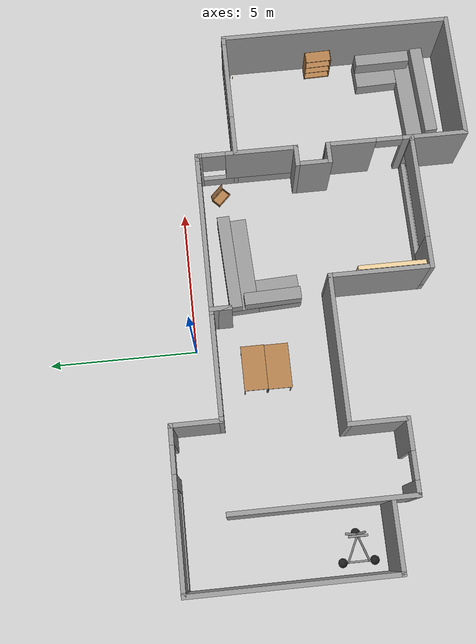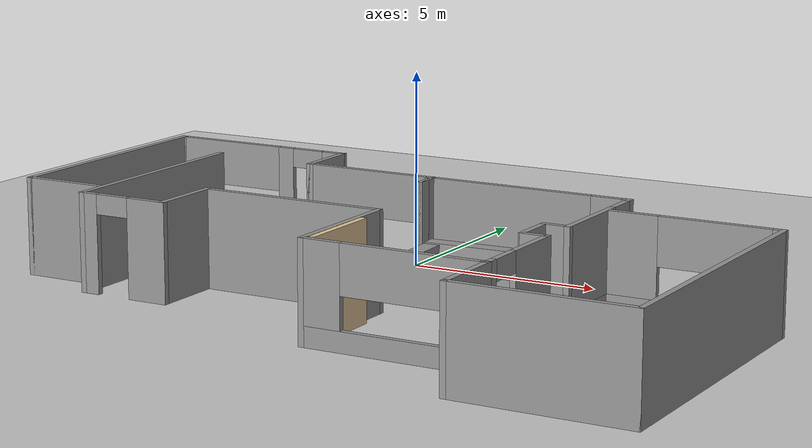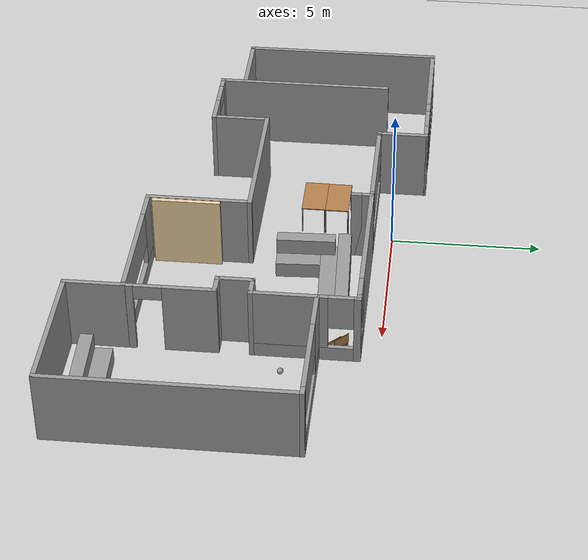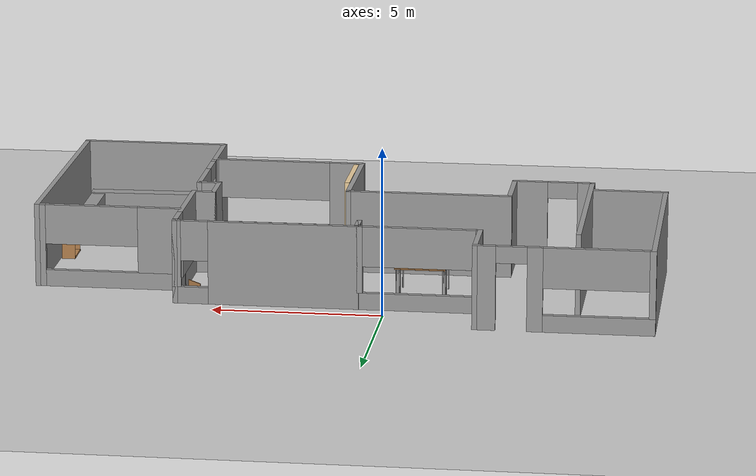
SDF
<sdf version="1.6">
 <world name="default">
  <plugin name="hello" filename="libhello.so"/>
  <light name="sun" type="directional">
   <pose>0 0 10 0 -0 0</pose>
   <diffuse>0.8 0.8 0.8 1</diffuse>
   <specular>0.2 0.2 0.2 1</specular>
   <attenuation>
    <range>1000</range>
    <constant>0.9</constant>
    <linear>0.01</linear>
    <quadratic>0.001</quadratic>
   </attenuation>
   <direction>-0.5 0.1 -0.9</direction>
   <spot><inner_angle>0</inner_angle><outer_angle>0</outer_angle><falloff>0</falloff></spot>
  </light>
  <model name="ground_plane">
   <static>1</static>
   <link name="link">
    <collision name="collision">
     <geometry><plane><normal>0 0 1</normal><size>100 100</size></plane></geometry>
     <surface>
      <contact><collide_bitmask>65535</collide_bitmask></contact>
      <friction><ode><mu>100</mu><mu2>50</mu2></ode></friction>
     </surface>
    </collision>
    <visual name="visual">
     <cast_shadows>0</cast_shadows>
     <geometry><plane><normal>0 0 1</normal><size>100 100</size></plane></geometry>
     <material>
      <script><uri>file://media/materials/scripts/gazebo.material</uri><name>Gazebo/Grey</name></script>
     </material>
    </visual>
   </link>
  </model>
  <gravity>0 0 -9.8</gravity>
  <magnetic_field>6e-06 2.3e-05 -4.2e-05</magnetic_field>
  <atmosphere type="adiabatic"/>
  <physics name="default_physics" default="0" type="ode">
   <max_step_size>0.001</max_step_size>
   <real_time_factor>1</real_time_factor>
   <real_time_update_rate>1000</real_time_update_rate>
  </physics>
  <scene><ambient>0.4 0.4 0.4 1</ambient><background>0.7 0.7 0.7 1</background><shadows>1</shadows></scene>
  <spherical_coordinates>
   <surface_model>EARTH_WGS84</surface_model>
   <latitude_deg>0</latitude_deg>
   <longitude_deg>0</longitude_deg>
   <elevation>0</elevation>
   <heading_deg>0</heading_deg>
  </spherical_coordinates>
  <model name="home">
   <pose>1.33369 -4.43199 0 0 -0 0</pose>
   <link name="Wall_1">
    <pose>-2.3 3.775 0 0 -0 0</pose>
    <visual name="Wall_1_Visual_0">
     <pose>-1.7772 0 1.25 0 -0 0</pose>
     <geometry><box><size>0.195597 0.15 2.5</size></box></geometry>
     <material>
      <script><uri>file://media/materials/scripts/gazebo.material</uri><name>Gazebo/Grey</name></script>
      <ambient>1 1 1 1</ambient>
     </material>
     <meta><layer>0</layer></meta>
    </visual>
    <collision name="Wall_1_Collision_0">
     <geometry><box><size>0.195597 0.15 2.5</size></box></geometry>
     <pose>-1.7772 0 1.25 0 -0 0</pose>
    </collision>
    <visual name="Wall_1_Visual_1">
     <pose>0.097799 0 0.25 0 -0 0</pose>
     <geometry><box><size>3.5544 0.15 0.5</size></box></geometry>
     <material>
      <script><uri>file://media/materials/scripts/gazebo.material</uri><name>Gazebo/Grey</name></script>
      <ambient>1 1 1 1</ambient>
     </material>
     <meta><layer>0</layer></meta>
    </visual>
    <collision name="Wall_1_Collision_1">
     <geometry><box><size>3.5544 0.15 0.5</size></box></geometry>
     <pose>0.097799 0 0.25 0 -0 0</pose>
    </collision>
    <visual name="Wall_1_Visual_2">
     <pose>1.74801 0 1.5 0 -0 0</pose>
     <geometry><box><size>0.253984 0.15 2</size></box></geometry>
     <material>
      <script><uri>file://media/materials/scripts/gazebo.material</uri><name>Gazebo/Grey</name></script>
      <ambient>1 1 1 1</ambient>
     </material>
     <meta><layer>0</layer></meta>
    </visual>
    <collision name="Wall_1_Collision_2">
     <geometry><box><size>0.253984 0.15 2</size></box></geometry>
     <pose>1.74801 0 1.5 0 -0 0</pose>
    </collision>
    <visual name="Wall_1_Visual_3">
     <pose>-0.029193 0 1.9 0 -0 0</pose>
     <geometry><box><size>3.30042 0.15 1.2</size></box></geometry>
     <material>
      <script><uri>file://media/materials/scripts/gazebo.material</uri><name>Gazebo/Grey</name></script>
      <ambient>1 1 1 1</ambient>
     </material>
     <meta><layer>0</layer></meta>
    </visual>
    <collision name="Wall_1_Collision_3">
     <geometry><box><size>3.30042 0.15 1.2</size></box></geometry>
     <pose>-0.029193 0 1.9 0 -0 0</pose>
    </collision>
   </link>
   <link name="Wall_10">
    <pose>2.55 -3.525 0 0 -0 3.14159</pose>
    <visual name="Wall_10_Visual_0">
     <pose>-2.27293 0 1.25 0 -0 0</pose>
     <geometry><box><size>0.204144 0.15 2.5</size></box></geometry>
     <material>
      <script><uri>file://media/materials/scripts/gazebo.material</uri><name>Gazebo/Grey</name></script>
      <ambient>1 1 1 1</ambient>
     </material>
     <meta><layer>0</layer></meta>
    </visual>
    <collision name="Wall_10_Collision_0">
     <geometry><box><size>0.204144 0.15 2.5</size></box></geometry>
     <pose>-2.27293 0 1.25 0 -0 0</pose>
    </collision>
    <visual name="Wall_10_Visual_1">
     <pose>0.102072 0 0.25 0 -0 0</pose>
     <geometry><box><size>4.54586 0.15 0.5</size></box></geometry>
     <material>
      <script><uri>file://media/materials/scripts/gazebo.material</uri><name>Gazebo/Grey</name></script>
      <ambient>1 1 1 1</ambient>
     </material>
     <meta><layer>0</layer></meta>
    </visual>
    <collision name="Wall_10_Collision_1">
     <geometry><box><size>4.54586 0.15 0.5</size></box></geometry>
     <pose>0.102072 0 0.25 0 -0 0</pose>
    </collision>
    <visual name="Wall_10_Visual_2">
     <pose>1.83208 0 1.5 0 -0 0</pose>
     <geometry><box><size>1.08584 0.15 2</size></box></geometry>
     <material>
      <script><uri>file://media/materials/scripts/gazebo.material</uri><name>Gazebo/Grey</name></script>
      <ambient>1 1 1 1</ambient>
     </material>
     <meta><layer>0</layer></meta>
    </visual>
    <collision name="Wall_10_Collision_2">
     <geometry><box><size>1.08584 0.15 2</size></box></geometry>
     <pose>1.83208 0 1.5 0 -0 0</pose>
    </collision>
    <visual name="Wall_10_Visual_3">
     <pose>-0.440846 0 1.9 0 -0 0</pose>
     <geometry><box><size>3.46002 0.15 1.2</size></box></geometry>
     <material>
      <script><uri>file://media/materials/scripts/gazebo.material</uri><name>Gazebo/Grey</name></script>
      <ambient>1 1 1 1</ambient>
     </material>
     <meta><layer>0</layer></meta>
    </visual>
    <collision name="Wall_10_Collision_3">
     <geometry><box><size>3.46002 0.15 1.2</size></box></geometry>
     <pose>-0.440846 0 1.9 0 -0 0</pose>
    </collision>
   </link>
   <link name="Wall_11">
    <collision name="Wall_11_Collision">
     <geometry><box><size>3.5 0.15 2.5</size></box></geometry>
     <pose>0 0 1.25 0 -0 0</pose>
    </collision>
    <visual name="Wall_11_Visual">
     <pose>0 0 1.25 0 -0 0</pose>
     <geometry><box><size>3.5 0.15 2.5</size></box></geometry>
     <material>
      <script><uri>file://media/materials/scripts/gazebo.material</uri><name>Gazebo/Grey</name></script>
      <ambient>1 1 1 1</ambient>
     </material>
     <meta><layer>0</layer></meta>
    </visual>
    <pose>0.25 -1.85 0 0 -0 1.5708</pose>
   </link>
   <link name="Wall_12">
    <collision name="Wall_12_Collision">
     <geometry><box><size>5 0.15 2.5</size></box></geometry>
     <pose>0 0 1.25 0 -0 0</pose>
    </collision>
    <visual name="Wall_12_Visual">
     <pose>0 0 1.25 0 -0 0</pose>
     <geometry><box><size>5 0.15 2.5</size></box></geometry>
     <material>
      <script><uri>file://media/materials/scripts/gazebo.material</uri><name>Gazebo/Grey</name></script>
      <ambient>1 1 1 1</ambient>
     </material>
     <meta><layer>0</layer></meta>
    </visual>
    <pose>-2.175 -0.175 0 0 -0 3.14159</pose>
   </link>
   <link name="Wall_13">
    <collision name="Wall_13_Collision">
     <geometry><box><size>2 0.15 2.5</size></box></geometry>
     <pose>0 0 1.25 0 -0 0</pose>
    </collision>
    <visual name="Wall_13_Visual">
     <pose>0 0 1.25 0 -0 0</pose>
     <geometry><box><size>2 0.15 2.5</size></box></geometry>
     <material>
      <script><uri>file://media/materials/scripts/gazebo.material</uri><name>Gazebo/Grey</name></script>
      <ambient>1 1 1 1</ambient>
     </material>
     <meta><layer>0</layer></meta>
    </visual>
    <pose>-4.6 -1.1 0 0 -0 -1.5708</pose>
   </link>
   <link name="Wall_14">
    <pose>-5.775 -2.025 0 0 -0 3.14159</pose>
    <visual name="Wall_14_Visual_0">
     <pose>-0.710889 0 1.25 0 -0 0</pose>
     <geometry><box><size>1.07822 0.15 2.5</size></box></geometry>
     <material>
      <script><uri>file://media/materials/scripts/gazebo.material</uri><name>Gazebo/Grey</name></script>
      <ambient>1 1 1 1</ambient>
     </material>
     <meta><layer>0</layer></meta>
    </visual>
    <collision name="Wall_14_Collision_0">
     <geometry><box><size>1.07822 0.15 2.5</size></box></geometry>
     <pose>-0.710889 0 1.25 0 -0 0</pose>
    </collision>
    <visual name="Wall_14_Visual_1">
     <pose>0.989111 0 1.25 0 -0 0</pose>
     <geometry><box><size>0.521779 0.15 2.5</size></box></geometry>
     <material>
      <script><uri>file://media/materials/scripts/gazebo.material</uri><name>Gazebo/Grey</name></script>
      <ambient>1 1 1 1</ambient>
     </material>
     <meta><layer>0</layer></meta>
    </visual>
    <collision name="Wall_14_Collision_1">
     <geometry><box><size>0.521779 0.15 2.5</size></box></geometry>
     <pose>0.989111 0 1.25 0 -0 0</pose>
    </collision>
    <visual name="Wall_14_Visual_2">
     <pose>0.278221 0 2.25 0 -0 0</pose>
     <geometry><box><size>0.9 0.15 0.5</size></box></geometry>
     <material>
      <script><uri>file://media/materials/scripts/gazebo.material</uri><name>Gazebo/Grey</name></script>
      <ambient>1 1 1 1</ambient>
     </material>
     <meta><layer>0</layer></meta>
    </visual>
    <collision name="Wall_14_Collision_2">
     <geometry><box><size>0.9 0.15 0.5</size></box></geometry>
     <pose>0.278221 0 2.25 0 -0 0</pose>
    </collision>
   </link>
   <link name="Wall_15">
    <collision name="Wall_15_Collision">
     <geometry><box><size>6 0.15 2.5</size></box></geometry>
     <pose>0 0 1.25 0 -0 0</pose>
    </collision>
    <visual name="Wall_15_Visual">
     <pose>0 0 1.25 0 -0 0</pose>
     <geometry><box><size>6 0.15 2.5</size></box></geometry>
     <material>
      <script><uri>file://media/materials/scripts/gazebo.material</uri><name>Gazebo/Grey</name></script>
      <ambient>1 1 1 1</ambient>
     </material>
     <meta><layer>0</layer></meta>
    </visual>
    <pose>-6.95 0.9 0 0 -0 1.5708</pose>
   </link>
   <link name="Wall_17">
    <collision name="Wall_17_Collision">
     <geometry><box><size>1.75 0.15 2.5</size></box></geometry>
     <pose>0 0 1.25 0 -0 0</pose>
    </collision>
    <visual name="Wall_17_Visual">
     <pose>0 0 1.25 0 -0 0</pose>
     <geometry><box><size>1.75 0.15 2.5</size></box></geometry>
     <material>
      <script><uri>file://media/materials/scripts/gazebo.material</uri><name>Gazebo/Grey</name></script>
      <ambient>1 1 1 1</ambient>
     </material>
     <meta><layer>0</layer></meta>
    </visual>
    <pose>-4.1 4.575 0 0 -0 1.5708</pose>
   </link>
   <link name="Wall_18">
    <pose>-6.65 5.375 0 0 -0 3.14159</pose>
    <visual name="Wall_18_Visual_0">
     <pose>-2.28809 0 1.25 0 -0 0</pose>
     <geometry><box><size>0.673815 0.15 2.5</size></box></geometry>
     <material>
      <script><uri>file://media/materials/scripts/gazebo.material</uri><name>Gazebo/Grey</name></script>
      <ambient>1 1 1 1</ambient>
     </material>
     <meta><layer>0</layer></meta>
    </visual>
    <collision name="Wall_18_Collision_0">
     <geometry><box><size>0.673815 0.15 2.5</size></box></geometry>
     <pose>-2.28809 0 1.25 0 -0 0</pose>
    </collision>
    <visual name="Wall_18_Visual_1">
     <pose>-0.824481 0 1.25 0 -0 0</pose>
     <geometry><box><size>0.45341 0.15 2.5</size></box></geometry>
     <material>
      <script><uri>file://media/materials/scripts/gazebo.material</uri><name>Gazebo/Grey</name></script>
      <ambient>1 1 1 1</ambient>
     </material>
     <meta><layer>0</layer></meta>
    </visual>
    <collision name="Wall_18_Collision_1">
     <geometry><box><size>0.45341 0.15 2.5</size></box></geometry>
     <pose>-0.824481 0 1.25 0 -0 0</pose>
    </collision>
    <visual name="Wall_18_Visual_2">
     <pose>1.01361 0 0.25 0 -0 0</pose>
     <geometry><box><size>3.22278 0.15 0.5</size></box></geometry>
     <material>
      <script><uri>file://media/materials/scripts/gazebo.material</uri><name>Gazebo/Grey</name></script>
      <ambient>1 1 1 1</ambient>
     </material>
     <meta><layer>0</layer></meta>
    </visual>
    <collision name="Wall_18_Collision_2">
     <geometry><box><size>3.22278 0.15 0.5</size></box></geometry>
     <pose>1.01361 0 0.25 0 -0 0</pose>
    </collision>
    <visual name="Wall_18_Visual_3">
     <pose>2.53082 0 1.5 0 -0 0</pose>
     <geometry><box><size>0.188359 0.15 2</size></box></geometry>
     <material>
      <script><uri>file://media/materials/scripts/gazebo.material</uri><name>Gazebo/Grey</name></script>
      <ambient>1 1 1 1</ambient>
     </material>
     <meta><layer>0</layer></meta>
    </visual>
    <collision name="Wall_18_Collision_3">
     <geometry><box><size>0.188359 0.15 2</size></box></geometry>
     <pose>2.53082 0 1.5 0 -0 0</pose>
    </collision>
    <visual name="Wall_18_Visual_4">
     <pose>0.919433 0 1.9 0 -0 0</pose>
     <geometry><box><size>3.03442 0.15 1.2</size></box></geometry>
     <material>
      <script><uri>file://media/materials/scripts/gazebo.material</uri><name>Gazebo/Grey</name></script>
      <ambient>1 1 1 1</ambient>
     </material>
     <meta><layer>0</layer></meta>
    </visual>
    <collision name="Wall_18_Collision_4">
     <geometry><box><size>3.03442 0.15 1.2</size></box></geometry>
     <pose>0.919433 0 1.9 0 -0 0</pose>
    </collision>
    <visual name="Wall_18_Visual_5">
     <pose>-1.50118 0 2.25 0 -0 0</pose>
     <geometry><box><size>0.9 0.15 0.5</size></box></geometry>
     <material>
      <script><uri>file://media/materials/scripts/gazebo.material</uri><name>Gazebo/Grey</name></script>
      <ambient>1 1 1 1</ambient>
     </material>
     <meta><layer>0</layer></meta>
    </visual>
    <collision name="Wall_18_Collision_5">
     <geometry><box><size>0.9 0.15 0.5</size></box></geometry>
     <pose>-1.50118 0 2.25 0 -0 0</pose>
    </collision>
   </link>
   <link name="Wall_19">
    <collision name="Wall_19_Collision">
     <geometry><box><size>6.75 0.15 2.5</size></box></geometry>
     <pose>0 0 1.25 0 -0 0</pose>
    </collision>
    <visual name="Wall_19_Visual">
     <pose>0 0 1.25 0 -0 0</pose>
     <geometry><box><size>6.75 0.15 2.5</size></box></geometry>
     <material>
      <script><uri>file://media/materials/scripts/gazebo.material</uri><name>Gazebo/Grey</name></script>
      <ambient>1 1 1 1</ambient>
     </material>
     <meta><layer>0</layer></meta>
    </visual>
    <pose>-9.2 2.075 0 0 -0 -1.5708</pose>
   </link>
   <link name="Wall_2">
    <collision name="Wall_2_Collision">
     <geometry><box><size>0.75 0.15 2.5</size></box></geometry>
     <pose>0 0 1.25 0 -0 0</pose>
    </collision>
    <visual name="Wall_2_Visual">
     <pose>0 0 1.25 0 -0 0</pose>
     <geometry><box><size>0.75 0.15 2.5</size></box></geometry>
     <material>
      <script><uri>file://media/materials/scripts/gazebo.material</uri><name>Gazebo/Grey</name></script>
      <ambient>1 1 1 1</ambient>
     </material>
     <meta><layer>0</layer></meta>
    </visual>
    <pose>-0.5 3.475 0 0 -0 -1.5708</pose>
   </link>
   <link name="Wall_20">
    <collision name="Wall_20_Collision">
     <geometry><box><size>2.25 0.15 2.5</size></box></geometry>
     <pose>0 0 1.25 0 -0 0</pose>
    </collision>
    <visual name="Wall_20_Visual">
     <pose>0 0 1.25 0 -0 0</pose>
     <geometry><box><size>2.25 0.15 2.5</size></box></geometry>
     <material>
      <script><uri>file://media/materials/scripts/gazebo.material</uri><name>Gazebo/Grey</name></script>
      <ambient>1 1 1 1</ambient>
     </material>
     <meta><layer>0</layer></meta>
    </visual>
    <pose>-8.15 -1.225 0 0 -0 0</pose>
   </link>
   <link name="Wall_22">
    <collision name="Wall_22_Collision">
     <geometry><box><size>2 0.15 2.5</size></box></geometry>
     <pose>0 0 1.25 0 -0 0</pose>
    </collision>
    <visual name="Wall_22_Visual">
     <pose>0 0 1.25 0 -0 0</pose>
     <geometry><box><size>2 0.15 2.5</size></box></geometry>
     <material>
      <script><uri>file://media/materials/scripts/gazebo.material</uri><name>Gazebo/Grey</name></script>
      <ambient>1 1 1 1</ambient>
     </material>
     <meta><layer>0</layer></meta>
    </visual>
    <pose>4.85 -4.45 0 0 -0 -1.5708</pose>
   </link>
   <link name="Wall_23">
    <collision name="Wall_23_Collision">
     <geometry><box><size>4.5 0.15 2.5</size></box></geometry>
     <pose>0 0 1.25 0 -0 0</pose>
    </collision>
    <visual name="Wall_23_Visual">
     <pose>0 0 1.25 0 -0 0</pose>
     <geometry><box><size>4.5 0.15 2.5</size></box></geometry>
     <material>
      <script><uri>file://media/materials/scripts/gazebo.material</uri><name>Gazebo/Grey</name></script>
      <ambient>1 1 1 1</ambient>
     </material>
     <meta><layer>0</layer></meta>
    </visual>
    <pose>7.025 -5.375 0 0 -0 0</pose>
   </link>
   <link name="Wall_24">
    <collision name="Wall_24_Collision">
     <geometry><box><size>8 0.15 2.5</size></box></geometry>
     <pose>0 0 1.25 0 -0 0</pose>
    </collision>
    <visual name="Wall_24_Visual">
     <pose>0 0 1.25 0 -0 0</pose>
     <geometry><box><size>8 0.15 2.5</size></box></geometry>
     <material>
      <script><uri>file://media/materials/scripts/gazebo.material</uri><name>Gazebo/Grey</name></script>
      <ambient>1 1 1 1</ambient>
     </material>
     <meta><layer>0</layer></meta>
    </visual>
    <pose>9.2 -1.45 0 0 -0 1.5708</pose>
   </link>
   <link name="Wall_25">
    <pose>7.025 2.475 0 0 -0 3.14159</pose>
    <visual name="Wall_25_Visual_0">
     <pose>-2.08764 0 1.25 0 -0 0</pose>
     <geometry><box><size>0.324712 0.15 2.5</size></box></geometry>
     <material>
      <script><uri>file://media/materials/scripts/gazebo.material</uri><name>Gazebo/Grey</name></script>
      <ambient>1 1 1 1</ambient>
     </material>
     <meta><layer>0</layer></meta>
    </visual>
    <collision name="Wall_25_Collision_0">
     <geometry><box><size>0.324712 0.15 2.5</size></box></geometry>
     <pose>-2.08764 0 1.25 0 -0 0</pose>
    </collision>
    <visual name="Wall_25_Visual_1">
     <pose>0.162356 0 0.25 0 -0 0</pose>
     <geometry><box><size>4.17529 0.15 0.5</size></box></geometry>
     <material>
      <script><uri>file://media/materials/scripts/gazebo.material</uri><name>Gazebo/Grey</name></script>
      <ambient>1 1 1 1</ambient>
     </material>
     <meta><layer>0</layer></meta>
    </visual>
    <collision name="Wall_25_Collision_1">
     <geometry><box><size>4.17529 0.15 0.5</size></box></geometry>
     <pose>0.162356 0 0.25 0 -0 0</pose>
    </collision>
    <visual name="Wall_25_Visual_2">
     <pose>1.54656 0 1.5 0 -0 0</pose>
     <geometry><box><size>1.40687 0.15 2</size></box></geometry>
     <material>
      <script><uri>file://media/materials/scripts/gazebo.material</uri><name>Gazebo/Grey</name></script>
      <ambient>1 1 1 1</ambient>
     </material>
     <meta><layer>0</layer></meta>
    </visual>
    <collision name="Wall_25_Collision_2">
     <geometry><box><size>1.40687 0.15 2</size></box></geometry>
     <pose>1.54656 0 1.5 0 -0 0</pose>
    </collision>
    <visual name="Wall_25_Visual_3">
     <pose>-0.54108 0 1.9 0 -0 0</pose>
     <geometry><box><size>2.76842 0.15 1.2</size></box></geometry>
     <material>
      <script><uri>file://media/materials/scripts/gazebo.material</uri><name>Gazebo/Grey</name></script>
      <ambient>1 1 1 1</ambient>
     </material>
     <meta><layer>0</layer></meta>
    </visual>
    <collision name="Wall_25_Collision_3">
     <geometry><box><size>2.76842 0.15 1.2</size></box></geometry>
     <pose>-0.54108 0 1.9 0 -0 0</pose>
    </collision>
   </link>
   <link name="Wall_3">
    <collision name="Wall_3_Collision">
     <geometry><box><size>0.75 0.15 2.5</size></box></geometry>
     <pose>0 0 1.25 0 -0 0</pose>
    </collision>
    <visual name="Wall_3_Visual">
     <pose>0 0 1.25 0 -0 0</pose>
     <geometry><box><size>0.75 0.15 2.5</size></box></geometry>
     <material>
      <script><uri>file://media/materials/scripts/gazebo.material</uri><name>Gazebo/Grey</name></script>
      <ambient>1 1 1 1</ambient>
     </material>
     <meta><layer>0</layer></meta>
    </visual>
    <pose>-0.5 3.475 0 0 -0 1.5708</pose>
   </link>
   <link name="Wall_4">
    <pose>2.175 3.775 0 0 -0 0</pose>
    <visual name="Wall_4_Visual_0">
     <pose>-0.528672 0 1.25 0 -0 0</pose>
     <geometry><box><size>4.44266 0.15 2.5</size></box></geometry>
     <material>
      <script><uri>file://media/materials/scripts/gazebo.material</uri><name>Gazebo/Grey</name></script>
      <ambient>1 1 1 1</ambient>
     </material>
     <meta><layer>0</layer></meta>
    </visual>
    <collision name="Wall_4_Collision_0">
     <geometry><box><size>4.44266 0.15 2.5</size></box></geometry>
     <pose>-0.528672 0 1.25 0 -0 0</pose>
    </collision>
    <visual name="Wall_4_Visual_1">
     <pose>2.22133 0 0.25 0 -0 0</pose>
     <geometry><box><size>1.05734 0.15 0.5</size></box></geometry>
     <material>
      <script><uri>file://media/materials/scripts/gazebo.material</uri><name>Gazebo/Grey</name></script>
      <ambient>1 1 1 1</ambient>
     </material>
     <meta><layer>0</layer></meta>
    </visual>
    <collision name="Wall_4_Collision_1">
     <geometry><box><size>1.05734 0.15 0.5</size></box></geometry>
     <pose>2.22133 0 0.25 0 -0 0</pose>
    </collision>
    <visual name="Wall_4_Visual_2">
     <pose>2.62133 0 1.5 0 -0 0</pose>
     <geometry><box><size>0.257344 0.15 2</size></box></geometry>
     <material>
      <script><uri>file://media/materials/scripts/gazebo.material</uri><name>Gazebo/Grey</name></script>
      <ambient>1 1 1 1</ambient>
     </material>
     <meta><layer>0</layer></meta>
    </visual>
    <collision name="Wall_4_Collision_2">
     <geometry><box><size>0.257344 0.15 2</size></box></geometry>
     <pose>2.62133 0 1.5 0 -0 0</pose>
    </collision>
    <visual name="Wall_4_Visual_3">
     <pose>2.09266 0 1.9 0 -0 0</pose>
     <geometry><box><size>0.8 0.15 1.2</size></box></geometry>
     <material>
      <script><uri>file://media/materials/scripts/gazebo.material</uri><name>Gazebo/Grey</name></script>
      <ambient>1 1 1 1</ambient>
     </material>
     <meta><layer>0</layer></meta>
    </visual>
    <collision name="Wall_4_Collision_3">
     <geometry><box><size>0.8 0.15 1.2</size></box></geometry>
     <pose>2.09266 0 1.9 0 -0 0</pose>
    </collision>
   </link>
   <link name="Wall_5">
    <pose>4.85 2.1 0 0 -0 -1.5708</pose>
    <visual name="Wall_5_Visual_0">
     <pose>-1.63495 0 1.25 0 -0 0</pose>
     <geometry><box><size>0.230105 0.15 2.5</size></box></geometry>
     <material>
      <script><uri>file://media/materials/scripts/gazebo.material</uri><name>Gazebo/Grey</name></script>
      <ambient>1 1 1 1</ambient>
     </material>
     <meta><layer>0</layer></meta>
    </visual>
    <collision name="Wall_5_Collision_0">
     <geometry><box><size>0.230105 0.15 2.5</size></box></geometry>
     <pose>-1.63495 0 1.25 0 -0 0</pose>
    </collision>
    <visual name="Wall_5_Visual_1">
     <pose>0.115053 0 0.25 0 -0 0</pose>
     <geometry><box><size>3.26989 0.15 0.5</size></box></geometry>
     <material>
      <script><uri>file://media/materials/scripts/gazebo.material</uri><name>Gazebo/Grey</name></script>
      <ambient>1 1 1 1</ambient>
     </material>
     <meta><layer>0</layer></meta>
    </visual>
    <collision name="Wall_5_Collision_1">
     <geometry><box><size>3.26989 0.15 0.5</size></box></geometry>
     <pose>0.115053 0 0.25 0 -0 0</pose>
    </collision>
    <visual name="Wall_5_Visual_2">
     <pose>0.515053 0 1.5 0 -0 0</pose>
     <geometry><box><size>2.4699 0.15 2</size></box></geometry>
     <material>
      <script><uri>file://media/materials/scripts/gazebo.material</uri><name>Gazebo/Grey</name></script>
      <ambient>1 1 1 1</ambient>
     </material>
     <meta><layer>0</layer></meta>
    </visual>
    <collision name="Wall_5_Collision_2">
     <geometry><box><size>2.4699 0.15 2</size></box></geometry>
     <pose>0.515053 0 1.5 0 -0 0</pose>
    </collision>
    <visual name="Wall_5_Visual_3">
     <pose>-1.1199 0 1.9 0 -0 0</pose>
     <geometry><box><size>0.8 0.15 1.2</size></box></geometry>
     <material>
      <script><uri>file://media/materials/scripts/gazebo.material</uri><name>Gazebo/Grey</name></script>
      <ambient>1 1 1 1</ambient>
     </material>
     <meta><layer>0</layer></meta>
    </visual>
    <collision name="Wall_5_Collision_3">
     <geometry><box><size>0.8 0.15 1.2</size></box></geometry>
     <pose>-1.1199 0 1.9 0 -0 0</pose>
    </collision>
   </link>
   <link name="Wall_6">
    <collision name="Wall_6_Collision">
     <geometry><box><size>0.75 0.15 2.5</size></box></geometry>
     <pose>0 0 1.25 0 -0 0</pose>
    </collision>
    <visual name="Wall_6_Visual">
     <pose>0 0 1.25 0 -0 0</pose>
     <geometry><box><size>0.75 0.15 2.5</size></box></geometry>
     <material>
      <script><uri>file://media/materials/scripts/gazebo.material</uri><name>Gazebo/Grey</name></script>
      <ambient>1 1 1 1</ambient>
     </material>
     <meta><layer>0</layer></meta>
    </visual>
    <pose>4.55 0.425 0 0 -0 3.14159</pose>
   </link>
   <link name="Wall_7">
    <collision name="Wall_7_Collision">
     <geometry><box><size>1.25 0.15 2.5</size></box></geometry>
     <pose>0 0 1.25 0 -0 0</pose>
    </collision>
    <visual name="Wall_7_Visual">
     <pose>0 0 1.25 0 -0 0</pose>
     <geometry><box><size>1.25 0.15 2.5</size></box></geometry>
     <material>
      <script><uri>file://media/materials/scripts/gazebo.material</uri><name>Gazebo/Grey</name></script>
      <ambient>1 1 1 1</ambient>
     </material>
     <meta><layer>0</layer></meta>
    </visual>
    <pose>4.25 -0.125 0 0 -0 -1.5708</pose>
   </link>
   <link name="Wall_8">
    <collision name="Wall_8_Collision">
     <geometry><box><size>0.75 0.15 2.5</size></box></geometry>
     <pose>0 0 1.25 0 -0 0</pose>
    </collision>
    <visual name="Wall_8_Visual">
     <pose>0 0 1.25 0 -0 0</pose>
     <geometry><box><size>0.75 0.15 2.5</size></box></geometry>
     <material>
      <script><uri>file://media/materials/scripts/gazebo.material</uri><name>Gazebo/Grey</name></script>
      <ambient>1 1 1 1</ambient>
     </material>
     <meta><layer>0</layer></meta>
    </visual>
    <pose>4.55 -0.675 0 0 -0 0</pose>
   </link>
   <link name="Wall_9">
    <pose>4.85 -2.1 0 0 -0 -1.5708</pose>
    <visual name="Wall_9_Visual_0">
     <pose>-0.642425 0 1.25 0 -0 0</pose>
     <geometry><box><size>1.71515 0.15 2.5</size></box></geometry>
     <material>
      <script><uri>file://media/materials/scripts/gazebo.material</uri><name>Gazebo/Grey</name></script>
      <ambient>1 1 1 1</ambient>
     </material>
     <meta><layer>0</layer></meta>
    </visual>
    <collision name="Wall_9_Collision_0">
     <geometry><box><size>1.71515 0.15 2.5</size></box></geometry>
     <pose>-0.642425 0 1.25 0 -0 0</pose>
    </collision>
    <visual name="Wall_9_Visual_1">
     <pose>1.30757 0 1.25 0 -0 0</pose>
     <geometry><box><size>0.38485 0.15 2.5</size></box></geometry>
     <material>
      <script><uri>file://media/materials/scripts/gazebo.material</uri><name>Gazebo/Grey</name></script>
      <ambient>1 1 1 1</ambient>
     </material>
     <meta><layer>0</layer></meta>
    </visual>
    <collision name="Wall_9_Collision_1">
     <geometry><box><size>0.38485 0.15 2.5</size></box></geometry>
     <pose>1.30757 0 1.25 0 -0 0</pose>
    </collision>
    <visual name="Wall_9_Visual_2">
     <pose>0.66515 0 2.25 0 -0 0</pose>
     <geometry><box><size>0.9 0.15 0.5</size></box></geometry>
     <material>
      <script><uri>file://media/materials/scripts/gazebo.material</uri><name>Gazebo/Grey</name></script>
      <ambient>1 1 1 1</ambient>
     </material>
     <meta><layer>0</layer></meta>
    </visual>
    <collision name="Wall_9_Collision_2">
     <geometry><box><size>0.9 0.15 0.5</size></box></geometry>
     <pose>0.66515 0 2.25 0 -0 0</pose>
    </collision>
   </link>
   <static>1</static>
  </model>
  <model name="table">
   <static>1</static>
   <link name="link">
    <collision name="surface">
     <pose>0 0 1 0 -0 0</pose>
     <geometry><box><size>1.5 0.8 0.03</size></box></geometry>
     <surface><friction><ode><mu>0.6</mu><mu2>0.6</mu2></ode></friction></surface>
    </collision>
    <visual name="visual1">
     <pose>0 0 1 0 -0 0</pose>
     <geometry><box><size>1.5 0.8 0.03</size></box></geometry>
     <material>
      <script><uri>file://media/materials/scripts/gazebo.material</uri><name>Gazebo/Wood</name></script>
     </material>
    </visual>
    <collision name="front_left_leg">
     <pose>0.68 0.38 0.5 0 -0 0</pose>
     <geometry><cylinder><radius>0.02</radius><length>1</length></cylinder></geometry>
    </collision>
    <visual name="front_left_leg">
     <pose>0.68 0.38 0.5 0 -0 0</pose>
     <geometry><cylinder><radius>0.02</radius><length>1</length></cylinder></geometry>
     <material>
      <script><uri>file://media/materials/scripts/gazebo.material</uri><name>Gazebo/Grey</name></script>
     </material>
    </visual>
    <collision name="front_right_leg">
     <pose>0.68 -0.38 0.5 0 -0 0</pose>
     <geometry><cylinder><radius>0.02</radius><length>1</length></cylinder></geometry>
    </collision>
    <visual name="front_right_leg">
     <pose>0.68 -0.38 0.5 0 -0 0</pose>
     <geometry><cylinder><radius>0.02</radius><length>1</length></cylinder></geometry>
     <material>
      <script><uri>file://media/materials/scripts/gazebo.material</uri><name>Gazebo/Grey</name></script>
     </material>
    </visual>
    <collision name="back_right_leg">
     <pose>-0.68 -0.38 0.5 0 -0 0</pose>
     <geometry><cylinder><radius>0.02</radius><length>1</length></cylinder></geometry>
    </collision>
    <visual name="back_right_leg">
     <pose>-0.68 -0.38 0.5 0 -0 0</pose>
     <geometry><cylinder><radius>0.02</radius><length>1</length></cylinder></geometry>
     <material>
      <script><uri>file://media/materials/scripts/gazebo.material</uri><name>Gazebo/Grey</name></script>
     </material>
    </visual>
    <collision name="back_left_leg">
     <pose>-0.68 0.38 0.5 0 -0 0</pose>
     <geometry><cylinder><radius>0.02</radius><length>1</length></cylinder></geometry>
    </collision>
    <visual name="back_left_leg">
     <pose>-0.68 0.38 0.5 0 -0 0</pose>
     <geometry><cylinder><radius>0.02</radius><length>1</length></cylinder></geometry>
     <material>
      <script><uri>file://media/materials/scripts/gazebo.material</uri><name>Gazebo/Grey</name></script>
     </material>
    </visual>
   </link>
   <pose>-0.917423 -1.8949 0 0 -0 0</pose>
  </model>
  <model name="table_0">
   <static>1</static>
   <link name="link">
    <collision name="surface">
     <pose>0 0 1 0 -0 0</pose>
     <geometry><box><size>1.5 0.8 0.03</size></box></geometry>
     <surface><friction><ode><mu>0.6</mu><mu2>0.6</mu2></ode></friction></surface>
    </collision>
    <visual name="visual1">
     <pose>0 0 1 0 -0 0</pose>
     <geometry><box><size>1.5 0.8 0.03</size></box></geometry>
     <material>
      <script><uri>file://media/materials/scripts/gazebo.material</uri><name>Gazebo/Wood</name></script>
     </material>
    </visual>
    <collision name="front_left_leg">
     <pose>0.68 0.38 0.5 0 -0 0</pose>
     <geometry><cylinder><radius>0.02</radius><length>1</length></cylinder></geometry>
    </collision>
    <visual name="front_left_leg">
     <pose>0.68 0.38 0.5 0 -0 0</pose>
     <geometry><cylinder><radius>0.02</radius><length>1</length></cylinder></geometry>
     <material>
      <script><uri>file://media/materials/scripts/gazebo.material</uri><name>Gazebo/Grey</name></script>
     </material>
    </visual>
    <collision name="front_right_leg">
     <pose>0.68 -0.38 0.5 0 -0 0</pose>
     <geometry><cylinder><radius>0.02</radius><length>1</length></cylinder></geometry>
    </collision>
    <visual name="front_right_leg">
     <pose>0.68 -0.38 0.5 0 -0 0</pose>
     <geometry><cylinder><radius>0.02</radius><length>1</length></cylinder></geometry>
     <material>
      <script><uri>file://media/materials/scripts/gazebo.material</uri><name>Gazebo/Grey</name></script>
     </material>
    </visual>
    <collision name="back_right_leg">
     <pose>-0.68 -0.38 0.5 0 -0 0</pose>
     <geometry><cylinder><radius>0.02</radius><length>1</length></cylinder></geometry>
    </collision>
    <visual name="back_right_leg">
     <pose>-0.68 -0.38 0.5 0 -0 0</pose>
     <geometry><cylinder><radius>0.02</radius><length>1</length></cylinder></geometry>
     <material>
      <script><uri>file://media/materials/scripts/gazebo.material</uri><name>Gazebo/Grey</name></script>
     </material>
    </visual>
    <collision name="back_left_leg">
     <pose>-0.68 0.38 0.5 0 -0 0</pose>
     <geometry><cylinder><radius>0.02</radius><length>1</length></cylinder></geometry>
    </collision>
    <visual name="back_left_leg">
     <pose>-0.68 0.38 0.5 0 -0 0</pose>
     <geometry><cylinder><radius>0.02</radius><length>1</length></cylinder></geometry>
     <material>
      <script><uri>file://media/materials/scripts/gazebo.material</uri><name>Gazebo/Grey</name></script>
     </material>
    </visual>
   </link>
   <pose>-0.932979 -2.68394 0 0 -0 0</pose>
  </model>
  <model name="Sofa">
   <link name="link_0">
    <inertial>
     <mass>1.78921</mass>
     <inertia><ixx>0.19365</ixx><ixy>0</ixy><ixz>0</ixz><iyy>1.64196</iyy><iyz>0</iyz><izz>1.74651</izz></inertia>
    </inertial>
    <pose>0.515913 0.4827 -0.27126 0 -0 0</pose>
    <visual name="visual">
     <geometry><box><size>3.27317 1 0.546616</size></box></geometry>
     <material>
      <lighting>1</lighting>
      <script><uri>file://media/materials/scripts/gazebo.material</uri><name>Gazebo/Grey</name></script>
      <shader type="pixel"/>
      <emissive>0 0 0 1</emissive>
     </material>
    </visual>
    <collision name="collision">
     <geometry><box><size>3.27317 1 0.546616</size></box></geometry>
     <surface>
      <friction>
       <ode><mu>1</mu><mu2>1</mu2><fdir1>0 0 0</fdir1><slip1>0</slip1><slip2>0</slip2></ode>
       <torsional>
        <coefficient>1</coefficient>
        <patch_radius>0</patch_radius>
        <surface_radius>0</surface_radius>
        <use_patch_radius>1</use_patch_radius>
        <ode><slip>0</slip></ode>
       </torsional>
      </friction>
      <bounce><restitution_coefficient>0</restitution_coefficient><threshold>1e+06</threshold></bounce>
      <contact>
       <collide_without_contact>0</collide_without_contact>
       <collide_without_contact_bitmask>1</collide_without_contact_bitmask>
       <collide_bitmask>1</collide_bitmask>
       <ode>
        <soft_cfm>0</soft_cfm>
        <soft_erp>0.2</soft_erp>
        <kp>1e+13</kp>
        <kd>1</kd>
        <max_vel>0.01</max_vel>
        <min_depth>0</min_depth>
       </ode>
       <bullet>
        <split_impulse>1</split_impulse>
        <split_impulse_penetration_threshold>-0.01</split_impulse_penetration_threshold>
        <soft_cfm>0</soft_cfm>
        <soft_erp>0.2</soft_erp>
        <kp>1e+13</kp>
        <kd>1</kd>
       </bullet>
      </contact>
     </surface>
    </collision>
   </link>
   <link name="link_0_clone">
    <inertial>
     <mass>0.763707</mass>
     <inertia>
      <ixx>0.0306107</ixx>
      <ixy>0</ixy>
      <ixz>0</ixz>
      <iyy>0.700856</iyy>
      <iyz>0</iyz>
      <izz>0.693436</izz>
     </inertia>
    </inertial>
    <pose>0.515913 0.769281 0.275356 0 -0 0</pose>
    <visual name="visual">
     <geometry><box><size>3.27317 0.426838 0.546616</size></box></geometry>
     <material>
      <lighting>1</lighting>
      <script><uri>file://media/materials/scripts/gazebo.material</uri><name>Gazebo/Grey</name></script>
      <shader type="pixel"/>
      <emissive>0 0 0 1</emissive>
     </material>
    </visual>
    <collision name="collision">
     <geometry><box><size>3.27317 0.426838 0.546616</size></box></geometry>
     <surface>
      <friction>
       <ode><mu>1</mu><mu2>1</mu2><fdir1>0 0 0</fdir1><slip1>0</slip1><slip2>0</slip2></ode>
       <torsional>
        <coefficient>1</coefficient>
        <patch_radius>0</patch_radius>
        <surface_radius>0</surface_radius>
        <use_patch_radius>1</use_patch_radius>
        <ode><slip>0</slip></ode>
       </torsional>
      </friction>
      <bounce><restitution_coefficient>0</restitution_coefficient><threshold>1e+06</threshold></bounce>
      <contact>
       <collide_without_contact>0</collide_without_contact>
       <collide_without_contact_bitmask>1</collide_without_contact_bitmask>
       <collide_bitmask>1</collide_bitmask>
       <ode>
        <soft_cfm>0</soft_cfm>
        <soft_erp>0.2</soft_erp>
        <kp>1e+13</kp>
        <kd>1</kd>
        <max_vel>0.01</max_vel>
        <min_depth>0</min_depth>
       </ode>
       <bullet>
        <split_impulse>1</split_impulse>
        <split_impulse_penetration_threshold>-0.01</split_impulse_penetration_threshold>
        <soft_cfm>0</soft_cfm>
        <soft_erp>0.2</soft_erp>
        <kp>1e+13</kp>
        <kd>1</kd>
       </bullet>
      </contact>
     </surface>
    </collision>
   </link>
   <link name="link_0_clone_clone">
    <inertial>
     <mass>0.450951</mass>
     <inertia>
      <ixx>0.0180749</ixx>
      <ixy>0</ixy>
      <ixz>0</ixz>
      <iyy>0.151605</iyy>
      <iyz>0</iyz>
      <izz>0.147223</izz>
     </inertia>
    </inertial>
    <pose>-0.891825 -0.505668 0.267165 0 -0 1.5548</pose>
    <visual name="visual">
     <geometry><box><size>1.93274 0.426838 0.546616</size></box></geometry>
     <material>
      <lighting>1</lighting>
      <script><uri>file://media/materials/scripts/gazebo.material</uri><name>Gazebo/Grey</name></script>
      <shader type="pixel"/>
      <emissive>0 0 0 1</emissive>
     </material>
    </visual>
    <collision name="collision">
     <geometry><box><size>1.93274 0.426838 0.546616</size></box></geometry>
     <surface>
      <friction>
       <ode><mu>1</mu><mu2>1</mu2><fdir1>0 0 0</fdir1><slip1>0</slip1><slip2>0</slip2></ode>
       <torsional>
        <coefficient>1</coefficient>
        <patch_radius>0</patch_radius>
        <surface_radius>0</surface_radius>
        <use_patch_radius>1</use_patch_radius>
        <ode><slip>0</slip></ode>
       </torsional>
      </friction>
      <bounce><restitution_coefficient>0</restitution_coefficient><threshold>1e+06</threshold></bounce>
      <contact>
       <collide_without_contact>0</collide_without_contact>
       <collide_without_contact_bitmask>1</collide_without_contact_bitmask>
       <collide_bitmask>1</collide_bitmask>
       <ode>
        <soft_cfm>0</soft_cfm>
        <soft_erp>0.2</soft_erp>
        <kp>1e+13</kp>
        <kd>1</kd>
        <max_vel>0.01</max_vel>
        <min_depth>0</min_depth>
       </ode>
       <bullet>
        <split_impulse>1</split_impulse>
        <split_impulse_penetration_threshold>-0.01</split_impulse_penetration_threshold>
        <soft_cfm>0</soft_cfm>
        <soft_erp>0.2</soft_erp>
        <kp>1e+13</kp>
        <kd>1</kd>
       </bullet>
      </contact>
     </surface>
    </collision>
   </link>
   <link name="link_1">
    <inertial>
     <mass>0.773084</mass>
     <inertia>
      <ixx>0.155067</ixx>
      <ixy>0</ixy>
      <ixz>0</ixz>
      <iyy>0.0825363</iyy>
      <iyz>0</iyz>
      <izz>0.201378</izz>
     </inertia>
    </inertial>
    <pose>-0.620672 -0.746314 -0.27126 0 -0 0</pose>
    <visual name="visual">
     <geometry><box><size>1 1.45803 0.530235</size></box></geometry>
     <material>
      <lighting>1</lighting>
      <script><uri>file://media/materials/scripts/gazebo.material</uri><name>Gazebo/Grey</name></script>
      <shader type="pixel"/>
      <emissive>0 0 0 1</emissive>
     </material>
    </visual>
    <collision name="collision">
     <geometry><box><size>1 1.45803 0.530235</size></box></geometry>
     <surface>
      <friction>
       <ode><mu>1</mu><mu2>1</mu2><fdir1>0 0 0</fdir1><slip1>0</slip1><slip2>0</slip2></ode>
       <torsional>
        <coefficient>1</coefficient>
        <patch_radius>0</patch_radius>
        <surface_radius>0</surface_radius>
        <use_patch_radius>1</use_patch_radius>
        <ode><slip>0</slip></ode>
       </torsional>
      </friction>
      <bounce><restitution_coefficient>0</restitution_coefficient><threshold>1e+06</threshold></bounce>
      <contact>
       <collide_without_contact>0</collide_without_contact>
       <collide_without_contact_bitmask>1</collide_without_contact_bitmask>
       <collide_bitmask>1</collide_bitmask>
       <ode>
        <soft_cfm>0</soft_cfm>
        <soft_erp>0.2</soft_erp>
        <kp>1e+13</kp>
        <kd>1</kd>
        <max_vel>0.01</max_vel>
        <min_depth>0</min_depth>
       </ode>
       <bullet>
        <split_impulse>1</split_impulse>
        <split_impulse_penetration_threshold>-0.01</split_impulse_penetration_threshold>
        <soft_cfm>0</soft_cfm>
        <soft_erp>0.2</soft_erp>
        <kp>1e+13</kp>
        <kd>1</kd>
       </bullet>
      </contact>
     </surface>
    </collision>
   </link>
   <joint name="link_0_JOINT_0" type="revolute">
    <parent>link_0</parent>
    <child>link_1</child>
    <axis>
     <xyz>1 0 0</xyz>
     <limit>
      <lower>-1.79769e+308</lower>
      <upper>1.79769e+308</upper>
      <effort>-1</effort>
      <velocity>-1</velocity>
     </limit>
     <dynamics>
      <spring_reference>0</spring_reference>
      <spring_stiffness>0</spring_stiffness>
      <damping>0</damping>
     </dynamics>
     <use_parent_model_frame>0</use_parent_model_frame>
    </axis>
    <physics>
     <ode><limit><cfm>0</cfm><erp>0.2</erp></limit><suspension><cfm>0</cfm><erp>0.2</erp></suspension></ode>
    </physics>
   </joint>
   <joint name="link_0_JOINT_2" type="revolute">
    <parent>link_0</parent>
    <child>link_0_clone</child>
    <axis>
     <xyz>1 0 0</xyz>
     <limit>
      <lower>-1.79769e+308</lower>
      <upper>1.79769e+308</upper>
      <effort>-1</effort>
      <velocity>-1</velocity>
     </limit>
     <dynamics>
      <spring_reference>0</spring_reference>
      <spring_stiffness>0</spring_stiffness>
      <damping>0</damping>
     </dynamics>
     <use_parent_model_frame>0</use_parent_model_frame>
    </axis>
    <physics>
     <ode><limit><cfm>0</cfm><erp>0.2</erp></limit><suspension><cfm>0</cfm><erp>0.2</erp></suspension></ode>
    </physics>
   </joint>
   <joint name="link_1_JOINT_4" type="revolute">
    <parent>link_1</parent>
    <child>link_0_clone_clone</child>
    <axis>
     <xyz>1 0 0</xyz>
     <limit>
      <lower>-1.79769e+308</lower>
      <upper>1.79769e+308</upper>
      <effort>-1</effort>
      <velocity>-1</velocity>
     </limit>
     <dynamics>
      <spring_reference>0</spring_reference>
      <spring_stiffness>0</spring_stiffness>
      <damping>0</damping>
     </dynamics>
     <use_parent_model_frame>0</use_parent_model_frame>
    </axis>
    <physics>
     <ode><limit><cfm>0</cfm><erp>0.2</erp></limit><suspension><cfm>0</cfm><erp>0.2</erp></suspension></ode>
    </physics>
   </joint>
   <static>0</static>
   <pose>2.339 -2.21498 0.544563 1e-06 3e-06 0.046</pose>
  </model>
  <light name="user_point_light_0" type="point">
   <pose>1.96023 4.17821 1 0 -0 0</pose>
   <diffuse>0.5 0.5 0.5 1</diffuse>
   <specular>0.1 0.1 0.1 1</specular>
   <attenuation>
    <range>20</range>
    <constant>0.5</constant>
    <linear>0.01</linear>
    <quadratic>0.001</quadratic>
   </attenuation>
   <cast_shadows>0</cast_shadows>
   <direction>0 0 -1</direction>
   <spot><inner_angle>0</inner_angle><outer_angle>0</outer_angle><falloff>0</falloff></spot>
  </light>
  <model name="colored_wall">
   <pose>2.23233 -6.67504 0 0 -0 0</pose>
   <link name="Wall_0">
    <collision name="Wall_0_Collision">
     <geometry><box><size>2.25 0.15 2.5</size></box></geometry>
     <pose>0 0 1.25 0 -0 0</pose>
    </collision>
    <visual name="Wall_0_Visual">
     <pose>0 0 1.25 0 -0 0</pose>
     <geometry><box><size>2.25 0.15 2.5</size></box></geometry>
     <material>
      <script><uri>file://media/materials/scripts/gazebo.material</uri><name>Gazebo/Grey</name></script>
      <ambient>0.921569 0.807843 0.615686 1</ambient>
     </material>
     <meta><layer>0</layer></meta>
    </visual>
    <pose>-0.487512 0 0 0 -0 1.5708</pose>
   </link>
   <static>1</static>
  </model>
  <model name="Sofa_0">
   <link name="link_0">
    <inertial>
     <mass>1.78921</mass>
     <inertia><ixx>0.19365</ixx><ixy>0</ixy><ixz>0</ixz><iyy>1.64196</iyy><iyz>0</iyz><izz>1.74651</izz></inertia>
    </inertial>
    <pose>0.515913 0.4827 -0.27126 0 -0 0</pose>
    <visual name="visual">
     <geometry><box><size>3.27317 1 0.546616</size></box></geometry>
     <material>
      <lighting>1</lighting>
      <script><uri>file://media/materials/scripts/gazebo.material</uri><name>Gazebo/Grey</name></script>
      <shader type="pixel"/>
      <emissive>0 0 0 1</emissive>
     </material>
    </visual>
    <collision name="collision">
     <geometry><box><size>3.27317 1 0.546616</size></box></geometry>
     <surface>
      <friction>
       <ode><mu>1</mu><mu2>1</mu2><fdir1>0 0 0</fdir1><slip1>0</slip1><slip2>0</slip2></ode>
       <torsional>
        <coefficient>1</coefficient>
        <patch_radius>0</patch_radius>
        <surface_radius>0</surface_radius>
        <use_patch_radius>1</use_patch_radius>
        <ode><slip>0</slip></ode>
       </torsional>
      </friction>
      <bounce><restitution_coefficient>0</restitution_coefficient><threshold>1e+06</threshold></bounce>
      <contact>
       <collide_without_contact>0</collide_without_contact>
       <collide_without_contact_bitmask>1</collide_without_contact_bitmask>
       <collide_bitmask>1</collide_bitmask>
       <ode>
        <soft_cfm>0</soft_cfm>
        <soft_erp>0.2</soft_erp>
        <kp>1e+13</kp>
        <kd>1</kd>
        <max_vel>0.01</max_vel>
        <min_depth>0</min_depth>
       </ode>
       <bullet>
        <split_impulse>1</split_impulse>
        <split_impulse_penetration_threshold>-0.01</split_impulse_penetration_threshold>
        <soft_cfm>0</soft_cfm>
        <soft_erp>0.2</soft_erp>
        <kp>1e+13</kp>
        <kd>1</kd>
       </bullet>
      </contact>
     </surface>
    </collision>
   </link>
   <link name="link_0_clone">
    <inertial>
     <mass>0.763707</mass>
     <inertia>
      <ixx>0.0306107</ixx>
      <ixy>0</ixy>
      <ixz>0</ixz>
      <iyy>0.700856</iyy>
      <iyz>0</iyz>
      <izz>0.693436</izz>
     </inertia>
    </inertial>
    <pose>0.515913 0.769281 0.275356 0 -0 0</pose>
    <visual name="visual">
     <geometry><box><size>3.27317 0.426838 0.546616</size></box></geometry>
     <material>
      <lighting>1</lighting>
      <script><uri>file://media/materials/scripts/gazebo.material</uri><name>Gazebo/Grey</name></script>
      <shader type="pixel"/>
      <emissive>0 0 0 1</emissive>
     </material>
    </visual>
    <collision name="collision">
     <geometry><box><size>3.27317 0.426838 0.546616</size></box></geometry>
     <surface>
      <friction>
       <ode><mu>1</mu><mu2>1</mu2><fdir1>0 0 0</fdir1><slip1>0</slip1><slip2>0</slip2></ode>
       <torsional>
        <coefficient>1</coefficient>
        <patch_radius>0</patch_radius>
        <surface_radius>0</surface_radius>
        <use_patch_radius>1</use_patch_radius>
        <ode><slip>0</slip></ode>
       </torsional>
      </friction>
      <bounce><restitution_coefficient>0</restitution_coefficient><threshold>1e+06</threshold></bounce>
      <contact>
       <collide_without_contact>0</collide_without_contact>
       <collide_without_contact_bitmask>1</collide_without_contact_bitmask>
       <collide_bitmask>1</collide_bitmask>
       <ode>
        <soft_cfm>0</soft_cfm>
        <soft_erp>0.2</soft_erp>
        <kp>1e+13</kp>
        <kd>1</kd>
        <max_vel>0.01</max_vel>
        <min_depth>0</min_depth>
       </ode>
       <bullet>
        <split_impulse>1</split_impulse>
        <split_impulse_penetration_threshold>-0.01</split_impulse_penetration_threshold>
        <soft_cfm>0</soft_cfm>
        <soft_erp>0.2</soft_erp>
        <kp>1e+13</kp>
        <kd>1</kd>
       </bullet>
      </contact>
     </surface>
    </collision>
   </link>
   <link name="link_0_clone_clone">
    <inertial>
     <mass>0.450951</mass>
     <inertia>
      <ixx>0.0180749</ixx>
      <ixy>0</ixy>
      <ixz>0</ixz>
      <iyy>0.151605</iyy>
      <iyz>0</iyz>
      <izz>0.147223</izz>
     </inertia>
    </inertial>
    <pose>-0.891825 -0.505668 0.267165 0 -0 1.5548</pose>
    <visual name="visual">
     <geometry><box><size>1.93274 0.426838 0.546616</size></box></geometry>
     <material>
      <lighting>1</lighting>
      <script><uri>file://media/materials/scripts/gazebo.material</uri><name>Gazebo/Grey</name></script>
      <shader type="pixel"/>
      <emissive>0 0 0 1</emissive>
     </material>
    </visual>
    <collision name="collision">
     <geometry><box><size>1.93274 0.426838 0.546616</size></box></geometry>
     <surface>
      <friction>
       <ode><mu>1</mu><mu2>1</mu2><fdir1>0 0 0</fdir1><slip1>0</slip1><slip2>0</slip2></ode>
       <torsional>
        <coefficient>1</coefficient>
        <patch_radius>0</patch_radius>
        <surface_radius>0</surface_radius>
        <use_patch_radius>1</use_patch_radius>
        <ode><slip>0</slip></ode>
       </torsional>
      </friction>
      <bounce><restitution_coefficient>0</restitution_coefficient><threshold>1e+06</threshold></bounce>
      <contact>
       <collide_without_contact>0</collide_without_contact>
       <collide_without_contact_bitmask>1</collide_without_contact_bitmask>
       <collide_bitmask>1</collide_bitmask>
       <ode>
        <soft_cfm>0</soft_cfm>
        <soft_erp>0.2</soft_erp>
        <kp>1e+13</kp>
        <kd>1</kd>
        <max_vel>0.01</max_vel>
        <min_depth>0</min_depth>
       </ode>
       <bullet>
        <split_impulse>1</split_impulse>
        <split_impulse_penetration_threshold>-0.01</split_impulse_penetration_threshold>
        <soft_cfm>0</soft_cfm>
        <soft_erp>0.2</soft_erp>
        <kp>1e+13</kp>
        <kd>1</kd>
       </bullet>
      </contact>
     </surface>
    </collision>
   </link>
   <link name="link_1">
    <inertial>
     <mass>0.773084</mass>
     <inertia>
      <ixx>0.155067</ixx>
      <ixy>0</ixy>
      <ixz>0</ixz>
      <iyy>0.0825363</iyy>
      <iyz>0</iyz>
      <izz>0.201378</izz>
     </inertia>
    </inertial>
    <pose>-0.620672 -0.746314 -0.27126 0 -0 0</pose>
    <visual name="visual">
     <geometry><box><size>1 1.45803 0.530235</size></box></geometry>
     <material>
      <lighting>1</lighting>
      <script><uri>file://media/materials/scripts/gazebo.material</uri><name>Gazebo/Grey</name></script>
      <shader type="pixel"/>
      <emissive>0 0 0 1</emissive>
     </material>
    </visual>
    <collision name="collision">
     <geometry><box><size>1 1.45803 0.530235</size></box></geometry>
     <surface>
      <friction>
       <ode><mu>1</mu><mu2>1</mu2><fdir1>0 0 0</fdir1><slip1>0</slip1><slip2>0</slip2></ode>
       <torsional>
        <coefficient>1</coefficient>
        <patch_radius>0</patch_radius>
        <surface_radius>0</surface_radius>
        <use_patch_radius>1</use_patch_radius>
        <ode><slip>0</slip></ode>
       </torsional>
      </friction>
      <bounce><restitution_coefficient>0</restitution_coefficient><threshold>1e+06</threshold></bounce>
      <contact>
       <collide_without_contact>0</collide_without_contact>
       <collide_without_contact_bitmask>1</collide_without_contact_bitmask>
       <collide_bitmask>1</collide_bitmask>
       <ode>
        <soft_cfm>0</soft_cfm>
        <soft_erp>0.2</soft_erp>
        <kp>1e+13</kp>
        <kd>1</kd>
        <max_vel>0.01</max_vel>
        <min_depth>0</min_depth>
       </ode>
       <bullet>
        <split_impulse>1</split_impulse>
        <split_impulse_penetration_threshold>-0.01</split_impulse_penetration_threshold>
        <soft_cfm>0</soft_cfm>
        <soft_erp>0.2</soft_erp>
        <kp>1e+13</kp>
        <kd>1</kd>
       </bullet>
      </contact>
     </surface>
    </collision>
   </link>
   <joint name="link_0_JOINT_0" type="revolute">
    <parent>link_0</parent>
    <child>link_1</child>
    <axis>
     <xyz>1 0 0</xyz>
     <limit>
      <lower>-1.79769e+308</lower>
      <upper>1.79769e+308</upper>
      <effort>-1</effort>
      <velocity>-1</velocity>
     </limit>
     <dynamics>
      <spring_reference>0</spring_reference>
      <spring_stiffness>0</spring_stiffness>
      <damping>0</damping>
     </dynamics>
     <use_parent_model_frame>0</use_parent_model_frame>
    </axis>
    <physics>
     <ode><limit><cfm>0</cfm><erp>0.2</erp></limit><suspension><cfm>0</cfm><erp>0.2</erp></suspension></ode>
    </physics>
   </joint>
   <joint name="link_0_JOINT_2" type="revolute">
    <parent>link_0</parent>
    <child>link_0_clone</child>
    <axis>
     <xyz>1 0 0</xyz>
     <limit>
      <lower>-1.79769e+308</lower>
      <upper>1.79769e+308</upper>
      <effort>-1</effort>
      <velocity>-1</velocity>
     </limit>
     <dynamics>
      <spring_reference>0</spring_reference>
      <spring_stiffness>0</spring_stiffness>
      <damping>0</damping>
     </dynamics>
     <use_parent_model_frame>0</use_parent_model_frame>
    </axis>
    <physics>
     <ode><limit><cfm>0</cfm><erp>0.2</erp></limit><suspension><cfm>0</cfm><erp>0.2</erp></suspension></ode>
    </physics>
   </joint>
   <joint name="link_1_JOINT_4" type="revolute">
    <parent>link_1</parent>
    <child>link_0_clone_clone</child>
    <axis>
     <xyz>1 0 0</xyz>
     <limit>
      <lower>-1.79769e+308</lower>
      <upper>1.79769e+308</upper>
      <effort>-1</effort>
      <velocity>-1</velocity>
     </limit>
     <dynamics>
      <spring_reference>0</spring_reference>
      <spring_stiffness>0</spring_stiffness>
      <damping>0</damping>
     </dynamics>
     <use_parent_model_frame>0</use_parent_model_frame>
    </axis>
    <physics>
     <ode><limit><cfm>0</cfm><erp>0.2</erp></limit><suspension><cfm>0</cfm><erp>0.2</erp></suspension></ode>
    </physics>
   </joint>
   <static>0</static>
   <pose>9.12328 -8.19479 0.544568 8e-06 -0 -3.11228</pose>
  </model>
  <model name="my_ball">
   <link name="link_0">
    <inertial>
     <mass>1</mass>
     <inertia><ixx>0.1</ixx><ixy>0</ixy><ixz>0</ixz><iyy>0.1</iyy><iyz>0</iyz><izz>0.1</izz></inertia>
    </inertial>
    <visual name="visual">
     <geometry><sphere><radius>0.1</radius></sphere></geometry>
     <material>
      <lighting>1</lighting>
      <script><uri>file://media/materials/scripts/gazebo.material</uri><name>Gazebo/Grey</name></script>
      <shader type="pixel"><normal_map>__default__</normal_map></shader>
      <ambient>1 1 1 1</ambient>
      <diffuse>1 1 1 1</diffuse>
      <specular>1 1 1 1</specular>
      <emissive>0 0 0 1</emissive>
     </material>
    </visual>
    <collision name="collision">
     <geometry><sphere><radius>0.1</radius></sphere></geometry>
     <surface>
      <friction>
       <ode><mu>1</mu><mu2>1</mu2><fdir1>0 0 0</fdir1><slip1>0</slip1><slip2>0</slip2></ode>
       <torsional>
        <coefficient>1</coefficient>
        <patch_radius>0</patch_radius>
        <surface_radius>0</surface_radius>
        <use_patch_radius>1</use_patch_radius>
        <ode><slip>0</slip></ode>
       </torsional>
      </friction>
      <bounce><restitution_coefficient>0</restitution_coefficient><threshold>1e+06</threshold></bounce>
      <contact>
       <collide_without_contact>0</collide_without_contact>
       <collide_without_contact_bitmask>1</collide_without_contact_bitmask>
       <collide_bitmask>1</collide_bitmask>
       <ode>
        <soft_cfm>0</soft_cfm>
        <soft_erp>0.2</soft_erp>
        <kp>1e+13</kp>
        <kd>1</kd>
        <max_vel>0.01</max_vel>
        <min_depth>0</min_depth>
       </ode>
       <bullet>
        <split_impulse>1</split_impulse>
        <split_impulse_penetration_threshold>-0.01</split_impulse_penetration_threshold>
        <soft_cfm>0</soft_cfm>
        <soft_erp>0.2</soft_erp>
        <kp>1e+13</kp>
        <kd>1</kd>
       </bullet>
      </contact>
     </surface>
    </collision>
   </link>
   <static>0</static>
   <pose>7.03331 -3.01641 0.1 0 -0 0</pose>
  </model>
  <model name="bookshelf">
   <static>1</static>
   <link name="link">
    <inertial><mass>1</mass></inertial>
    <collision name="back">
     <pose>0 0.005 0.6 0 -0 0</pose>
     <geometry><box><size>0.9 0.01 1.2</size></box></geometry>
    </collision>
    <visual name="visual1">
     <pose>0 0.005 0.6 0 -0 0</pose>
     <geometry><box><size>0.9 0.01 1.2</size></box></geometry>
     <material>
      <script><uri>file://media/materials/scripts/gazebo.material</uri><name>Gazebo/Wood</name></script>
     </material>
    </visual>
    <collision name="left_side">
     <pose>0.45 -0.195 0.6 0 -0 0</pose>
     <geometry><box><size>0.02 0.4 1.2</size></box></geometry>
    </collision>
    <visual name="visual2">
     <pose>0.45 -0.195 0.6 0 -0 0</pose>
     <geometry><box><size>0.02 0.4 1.2</size></box></geometry>
     <material>
      <script><uri>file://media/materials/scripts/gazebo.material</uri><name>Gazebo/Wood</name></script>
     </material>
    </visual>
    <collision name="right_side">
     <pose>-0.45 -0.195 0.6 0 -0 0</pose>
     <geometry><box><size>0.02 0.4 1.2</size></box></geometry>
    </collision>
    <visual name="visual3">
     <pose>-0.45 -0.195 0.6 0 -0 0</pose>
     <geometry><box><size>0.02 0.4 1.2</size></box></geometry>
     <material>
      <script><uri>file://media/materials/scripts/gazebo.material</uri><name>Gazebo/Wood</name></script>
     </material>
    </visual>
    <collision name="bottom">
     <pose>0 -0.195 0.03 0 -0 0</pose>
     <geometry><box><size>0.88 0.4 0.06</size></box></geometry>
    </collision>
    <visual name="visual4">
     <pose>0 -0.195 0.03 0 -0 0</pose>
     <geometry><box><size>0.88 0.4 0.06</size></box></geometry>
     <material>
      <script><uri>file://media/materials/scripts/gazebo.material</uri><name>Gazebo/Wood</name></script>
     </material>
    </visual>
    <collision name="top">
     <pose>0 -0.195 1.19 0 -0 0</pose>
     <geometry><box><size>0.88 0.4 0.02</size></box></geometry>
    </collision>
    <visual name="visual5">
     <pose>0 -0.195 1.19 0 -0 0</pose>
     <geometry><box><size>0.88 0.4 0.02</size></box></geometry>
     <material>
      <script><uri>file://media/materials/scripts/gazebo.material</uri><name>Gazebo/Wood</name></script>
     </material>
    </visual>
    <collision name="low_shelf">
     <pose>0 -0.195 0.43 0 -0 0</pose>
     <geometry><box><size>0.88 0.4 0.02</size></box></geometry>
    </collision>
    <visual name="visual6">
     <pose>0 -0.195 0.43 0 -0 0</pose>
     <geometry><box><size>0.88 0.4 0.02</size></box></geometry>
     <material>
      <script><uri>file://media/materials/scripts/gazebo.material</uri><name>Gazebo/Wood</name></script>
     </material>
    </visual>
    <collision name="high_shelf">
     <pose>0 -0.195 0.8 0 -0 0</pose>
     <geometry><box><size>0.88 0.4 0.02</size></box></geometry>
    </collision>
    <visual name="visual7">
     <pose>0 -0.195 0.8 0 -0 0</pose>
     <geometry><box><size>0.88 0.4 0.02</size></box></geometry>
     <material>
      <script><uri>file://media/materials/scripts/gazebo.material</uri><name>Gazebo/Wood</name></script>
     </material>
    </visual>
   </link>
   <pose>10.424 -5.33684 0 0 0 -1.54381</pose>
  </model>
  <model name="trisphere_cycle">
   <link name="frame">
    <pose>-0.408559 0 0.385023 0 -0.522021 0</pose>
    <inertial>
     <mass>10</mass>
     <inertia><ixx>0.228</ixx><iyy>0.743521</iyy><izz>0.965521</izz><ixy>0</ixy><ixz>0</ixz><iyz>0</iyz></inertia>
    </inertial>
    <collision name="axle_collision">
     <pose>-0.471335 0 0 1.5708 -0 0</pose>
     <geometry><cylinder><length>1.03923</length><radius>0.03</radius></cylinder></geometry>
    </collision>
    <visual name="axle_visual">
     <pose>-0.471335 0 0 1.5708 -0 0</pose>
     <geometry><cylinder><length>1.03923</length><radius>0.03</radius></cylinder></geometry>
     <material>
      <script><uri>file://media/materials/scripts/gazebo.material</uri><name>Gazebo/Grey</name></script>
     </material>
    </visual>
    <collision name="frame_left_collision">
     <pose>0 0.171552 0 -2.79253 1.57079 3.14159</pose>
     <geometry><cylinder><length>1.00317</length><radius>0.03</radius></cylinder></geometry>
    </collision>
    <visual name="frame_left_visual">
     <pose>0 0.171552 0 -2.79253 1.57079 3.14159</pose>
     <geometry><cylinder><length>1.00317</length><radius>0.03</radius></cylinder></geometry>
     <material>
      <script><uri>file://media/materials/scripts/gazebo.material</uri><name>Gazebo/Grey</name></script>
     </material>
    </visual>
    <collision name="frame_right_collision">
     <pose>0 -0.171552 0 2.79253 1.57079 -3.14159</pose>
     <geometry><cylinder><length>1.00317</length><radius>0.03</radius></cylinder></geometry>
    </collision>
    <visual name="frame_right_visual">
     <pose>0 -0.171552 0 2.79253 1.57079 -3.14159</pose>
     <geometry><cylinder><length>1.00317</length><radius>0.03</radius></cylinder></geometry>
     <material>
      <script><uri>file://media/materials/scripts/gazebo.material</uri><name>Gazebo/Grey</name></script>
     </material>
    </visual>
   </link>
   <link name="fork">
    <pose>0.041441 0 0.385023 0 -0.174533 0</pose>
    <inertial>
     <mass>3</mass>
     <inertia>
      <ixx>0.158203</ixx>
      <iyy>0.0583594</iyy>
      <izz>0.102656</izz>
      <ixy>0</ixy>
      <ixz>0</ixz>
      <iyz>0</iyz>
     </inertia>
    </inertial>
    <collision name="handlebars_collision">
     <pose>0 0 0.397748 1.5708 -0 0</pose>
     <geometry><cylinder><length>0.636396</length><radius>0.0375</radius></cylinder></geometry>
    </collision>
    <visual name="handlebars_visual">
     <pose>0 0 0.397748 1.5708 -0 0</pose>
     <geometry><cylinder><length>0.636396</length><radius>0.0375</radius></cylinder></geometry>
     <material>
      <script><uri>file://media/materials/scripts/gazebo.material</uri><name>Gazebo/Grey</name></script>
     </material>
    </visual>
    <collision name="headtube_collision">
     <pose>0 0 0.238649 0 -0 0</pose>
     <geometry><cylinder><length>0.318198</length><radius>0.0375</radius></cylinder></geometry>
    </collision>
    <visual name="headtube_visual">
     <pose>0 0 0.238649 0 -0 0</pose>
     <geometry><cylinder><length>0.318198</length><radius>0.0375</radius></cylinder></geometry>
     <material>
      <script><uri>file://media/materials/scripts/gazebo.material</uri><name>Gazebo/Grey</name></script>
     </material>
    </visual>
    <collision name="spindle_collision">
     <pose>0 0 -0.238649 1.5708 -0 0</pose>
     <geometry><cylinder><length>0.636396</length><radius>0.015</radius></cylinder></geometry>
    </collision>
    <visual name="spindle_visual">
     <pose>0 0 -0.238649 1.5708 -0 0</pose>
     <geometry><cylinder><length>0.636396</length><radius>0.015</radius></cylinder></geometry>
     <material>
      <script><uri>file://media/materials/scripts/gazebo.material</uri><name>Gazebo/Grey</name></script>
     </material>
    </visual>
    <collision name="fork_left_collision">
     <pose>0 0.159099 -0.07955 0.785398 -0 0</pose>
     <geometry><cylinder><length>0.45</length><radius>0.0375</radius></cylinder></geometry>
    </collision>
    <visual name="fork_left_visual">
     <pose>0 0.159099 -0.07955 0.785398 -0 0</pose>
     <geometry><cylinder><length>0.45</length><radius>0.0375</radius></cylinder></geometry>
     <material>
      <script><uri>file://media/materials/scripts/gazebo.material</uri><name>Gazebo/Grey</name></script>
     </material>
    </visual>
    <collision name="fork_right_collision">
     <pose>0 -0.159099 -0.07955 -0.785398 0 0</pose>
     <geometry><cylinder><length>0.45</length><radius>0.0375</radius></cylinder></geometry>
    </collision>
    <visual name="fork_right_visual">
     <pose>0 -0.159099 -0.07955 -0.785398 0 0</pose>
     <geometry><cylinder><length>0.45</length><radius>0.0375</radius></cylinder></geometry>
     <material>
      <script><uri>file://media/materials/scripts/gazebo.material</uri><name>Gazebo/Grey</name></script>
     </material>
    </visual>
   </link>
   <link name="wheel_front">
    <pose>0.082882 0 0.15 0 -0 0</pose>
    <inertial>
     <mass>0.5</mass>
     <inertia><ixx>0.0045</ixx><iyy>0.0045</iyy><izz>0.0045</izz><ixy>0</ixy><ixz>0</ixz><iyz>0</iyz></inertia>
    </inertial>
    <collision name="collision">
     <geometry><sphere><radius>0.15</radius></sphere></geometry>
     <surface><contact><ode><kp>1e+08</kp><kd>1</kd><min_depth>0.0005</min_depth></ode></contact></surface>
    </collision>
    <visual name="visual">
     <geometry><sphere><radius>0.15</radius></sphere></geometry>
     <material>
      <script><uri>file://media/materials/scripts/gazebo.material</uri><name>Gazebo/Black</name></script>
     </material>
    </visual>
   </link>
   <joint name="wheel_front_steer" type="revolute">
    <parent>frame</parent>
    <child>fork</child>
    <axis>
     <xyz>0 0 1</xyz>
     <limit><lower>-0.959931</lower><upper>0.959931</upper></limit>
     <use_parent_model_frame>0</use_parent_model_frame>
     <dynamics><spring_reference>0</spring_reference><spring_stiffness>0</spring_stiffness></dynamics>
    </axis>
   </joint>
   <joint name="wheel_front_spin" type="revolute">
    <parent>fork</parent>
    <child>wheel_front</child>
    <axis>
     <xyz>0 1 0</xyz>
     <use_parent_model_frame>0</use_parent_model_frame>
     <limit><lower>-1e+16</lower><upper>1e+16</upper></limit>
     <dynamics><spring_reference>0</spring_reference><spring_stiffness>0</spring_stiffness></dynamics>
    </axis>
   </joint>
   <link name="wheel_rear_left">
    <pose>-0.817118 0.519615 0.15 0 -0 0</pose>
    <inertial>
     <mass>0.5</mass>
     <inertia><ixx>0.0045</ixx><iyy>0.0045</iyy><izz>0.0045</izz><ixy>0</ixy><ixz>0</ixz><iyz>0</iyz></inertia>
    </inertial>
    <collision name="collision">
     <geometry><sphere><radius>0.15</radius></sphere></geometry>
     <surface><contact><ode><kp>1e+08</kp><kd>1</kd><min_depth>0.0005</min_depth></ode></contact></surface>
    </collision>
    <visual name="visual">
     <geometry><sphere><radius>0.15</radius></sphere></geometry>
     <material>
      <script><uri>file://media/materials/scripts/gazebo.material</uri><name>Gazebo/Black</name></script>
     </material>
    </visual>
   </link>
   <joint name="wheel_rear_left_spin" type="revolute">
    <parent>frame</parent>
    <child>wheel_rear_left</child>
    <axis>
     <xyz>0 1 0</xyz>
     <use_parent_model_frame>0</use_parent_model_frame>
     <limit><lower>-1e+16</lower><upper>1e+16</upper></limit>
     <dynamics><spring_reference>0</spring_reference><spring_stiffness>0</spring_stiffness></dynamics>
    </axis>
   </joint>
   <link name="wheel_rear_right">
    <pose>-0.817118 -0.519615 0.15 0 -0 0</pose>
    <inertial>
     <mass>0.5</mass>
     <inertia><ixx>0.0045</ixx><iyy>0.0045</iyy><izz>0.0045</izz><ixy>0</ixy><ixz>0</ixz><iyz>0</iyz></inertia>
    </inertial>
    <collision name="collision">
     <geometry><sphere><radius>0.15</radius></sphere></geometry>
     <surface><contact><ode><kp>1e+08</kp><kd>1</kd><min_depth>0.0005</min_depth></ode></contact></surface>
    </collision>
    <visual name="visual">
     <geometry><sphere><radius>0.15</radius></sphere></geometry>
     <material>
      <script><uri>file://media/materials/scripts/gazebo.material</uri><name>Gazebo/Black</name></script>
     </material>
    </visual>
   </link>
   <joint name="wheel_rear_right_spin" type="revolute">
    <parent>frame</parent>
    <child>wheel_rear_right</child>
    <axis>
     <xyz>0 1 0</xyz>
     <use_parent_model_frame>0</use_parent_model_frame>
     <limit><lower>-1e+16</lower><upper>1e+16</upper></limit>
     <dynamics><spring_reference>0</spring_reference><spring_stiffness>0</spring_stiffness></dynamics>
    </axis>
   </joint>
   <pose>-6.59104 -4.63278 -0.000501 -0 1e-06 -0.000202</pose>
  </model>
  <model name="wood_cube_10cm">
   <link name="link">
    <pose>0 0 0.05 0 -0 0</pose>
    <inertial>
     <mass>0.5167</mass>
     <inertia>
      <ixx>0.000861167</ixx>
      <ixy>0</ixy>
      <ixz>0</ixz>
      <iyy>0.000861167</iyy>
      <iyz>0</iyz>
      <izz>0.000861167</izz>
     </inertia>
    </inertial>
    <collision name="collision">
     <geometry><box><size>0.1 0.1 0.1</size></box></geometry>
     <surface>
      <contact>
       <poissons_ratio>0.347</poissons_ratio>
       <elastic_modulus>8.8e+09</elastic_modulus>
       <ode><kp>100000</kp><kd>100</kd><max_vel>100</max_vel><min_depth>0.001</min_depth></ode>
      </contact>
      <friction>
       <torsional>
        <coefficient>1</coefficient>
        <use_patch_radius>0</use_patch_radius>
        <surface_radius>0.01</surface_radius>
       </torsional>
      </friction>
     </surface>
    </collision>
    <visual name="visual">
     <geometry><box><size>0.1 0.1 0.1</size></box></geometry>
     <material>
      <script><uri>file://media/materials/scripts/gazebo.material</uri><name>Gazebo/Wood</name></script>
     </material>
    </visual>
   </link>
   <pose>10.3417 -2.09533 -0.001013 0 -0 0</pose>
  </model>
  <model name="wood_block_10_2_1cm">
   <link name="link">
    <pose>0 0 0.005 0 -0 0</pose>
    <inertial>
     <mass>0.0125</mass>
     <inertia>
      <ixx>7.55208e-07</ixx>
      <ixy>0</ixy>
      <ixz>0</ixz>
      <iyy>1.05208e-05</iyy>
      <iyz>0</iyz>
      <izz>1.10677e-05</izz>
     </inertia>
    </inertial>
    <collision name="collision">
     <geometry><box><size>0.1 0.025 0.01</size></box></geometry>
     <surface>
      <contact>
       <poissons_ratio>0.347</poissons_ratio>
       <elastic_modulus>8.8e+09</elastic_modulus>
       <ode><kp>100000</kp><kd>1</kd><max_vel>1</max_vel><min_depth>0.001</min_depth></ode>
      </contact>
      <friction>
       <torsional>
        <coefficient>1</coefficient>
        <use_patch_radius>0</use_patch_radius>
        <surface_radius>0.05</surface_radius>
       </torsional>
      </friction>
     </surface>
    </collision>
    <visual name="visual">
     <geometry><box><size>0.1 0.025 0.01</size></box></geometry>
     <material>
      <script><uri>file://media/materials/scripts/gazebo.material</uri><name>Gazebo/Wood</name></script>
     </material>
    </visual>
   </link>
   <pose>10.3256 -2.2273 -0.001 0 -0 0</pose>
  </model>
  <model name="wooden_case">
   <link name="base">
    <pose>0 0 0.024 0 -0 0</pose>
    <inertial>
     <pose>-0.022184 0 0.171592 0 -0 0</pose>
     <mass>3.96264</mass>
     <inertia>
      <ixx>0.213536</ixx>
      <ixy>0</ixy>
      <ixz>0.000779377</ixz>
      <iyy>0.0708943</iyy>
      <iyz>0</iyz>
      <izz>0.154604</izz>
     </inertia>
    </inertial>
    <collision name="collision_back">
     <pose>-0.053975 0 0.1778 0 -0 0</pose>
     <geometry><box><size>0.01905 0.5461 0.3175</size></box></geometry>
     <surface>
      <contact>
       <poissons_ratio>0.347</poissons_ratio>
       <elastic_modulus>8.8e+09</elastic_modulus>
       <ode><kp>100000</kp><kd>100</kd><max_vel>100</max_vel><min_depth>0.001</min_depth></ode>
      </contact>
      <friction>
       <torsional>
        <coefficient>1</coefficient>
        <use_patch_radius>0</use_patch_radius>
        <surface_radius>0.01</surface_radius>
       </torsional>
      </friction>
     </surface>
    </collision>
    <visual name="visual_back">
     <pose>-0.053975 0 0.1778 0 -0 0</pose>
     <geometry><box><size>0.01905 0.5461 0.3175</size></box></geometry>
     <material>
      <script><uri>file://media/materials/scripts/gazebo.material</uri><name>Gazebo/Wood</name></script>
     </material>
    </visual>
    <collision name="collision_bottom">
     <pose>0 0 0.009525 0 -0 0</pose>
     <geometry><box><size>0.127 0.5842 0.01905</size></box></geometry>
     <surface>
      <contact>
       <poissons_ratio>0.347</poissons_ratio>
       <elastic_modulus>8.8e+09</elastic_modulus>
       <ode><kp>100000</kp><kd>100</kd><max_vel>100</max_vel><min_depth>0.001</min_depth></ode>
      </contact>
      <friction>
       <torsional>
        <coefficient>1</coefficient>
        <use_patch_radius>0</use_patch_radius>
        <surface_radius>0.01</surface_radius>
       </torsional>
      </friction>
     </surface>
    </collision>
    <visual name="visual_bottom">
     <pose>0 0 0.009525 0 -0 0</pose>
     <geometry><box><size>0.127 0.5842 0.01905</size></box></geometry>
     <material>
      <script><uri>file://media/materials/scripts/gazebo.material</uri><name>Gazebo/Wood</name></script>
     </material>
    </visual>
    <collision name="collision_top">
     <pose>0 0 0.346075 0 -0 0</pose>
     <geometry><box><size>0.127 0.5842 0.01905</size></box></geometry>
     <surface>
      <contact>
       <poissons_ratio>0.347</poissons_ratio>
       <elastic_modulus>8.8e+09</elastic_modulus>
       <ode><kp>100000</kp><kd>100</kd><max_vel>100</max_vel><min_depth>0.001</min_depth></ode>
      </contact>
      <friction>
       <torsional>
        <coefficient>1</coefficient>
        <use_patch_radius>0</use_patch_radius>
        <surface_radius>0.01</surface_radius>
       </torsional>
      </friction>
     </surface>
    </collision>
    <visual name="visual_top">
     <pose>0 0 0.346075 0 -0 0</pose>
     <geometry><box><size>0.127 0.5842 0.01905</size></box></geometry>
     <material>
      <script><uri>file://media/materials/scripts/gazebo.material</uri><name>Gazebo/Wood</name></script>
     </material>
    </visual>
    <collision name="collision_left">
     <pose>0 -0.282575 0.1778 0 -0 0</pose>
     <geometry><box><size>0.127 0.01905 0.3175</size></box></geometry>
     <surface>
      <contact>
       <poissons_ratio>0.347</poissons_ratio>
       <elastic_modulus>8.8e+09</elastic_modulus>
       <ode><kp>100000</kp><kd>100</kd><max_vel>100</max_vel><min_depth>0.001</min_depth></ode>
      </contact>
      <friction>
       <torsional>
        <coefficient>1</coefficient>
        <use_patch_radius>0</use_patch_radius>
        <surface_radius>0.01</surface_radius>
       </torsional>
      </friction>
     </surface>
    </collision>
    <visual name="visual_left">
     <pose>0 -0.282575 0.1778 0 -0 0</pose>
     <geometry><box><size>0.127 0.01905 0.3175</size></box></geometry>
     <material>
      <script><uri>file://media/materials/scripts/gazebo.material</uri><name>Gazebo/Wood</name></script>
     </material>
    </visual>
    <collision name="collision_right">
     <pose>0 0.282575 0.1778 0 -0 0</pose>
     <geometry><box><size>0.127 0.01905 0.3175</size></box></geometry>
     <surface>
      <contact>
       <poissons_ratio>0.347</poissons_ratio>
       <elastic_modulus>8.8e+09</elastic_modulus>
       <ode><kp>100000</kp><kd>100</kd><max_vel>100</max_vel><min_depth>0.001</min_depth></ode>
      </contact>
      <friction>
       <torsional>
        <coefficient>1</coefficient>
        <use_patch_radius>0</use_patch_radius>
        <surface_radius>0.01</surface_radius>
       </torsional>
      </friction>
     </surface>
    </collision>
    <visual name="visual_right">
     <pose>0 0.282575 0.1778 0 -0 0</pose>
     <geometry><box><size>0.127 0.01905 0.3175</size></box></geometry>
     <material>
      <script><uri>file://media/materials/scripts/gazebo.material</uri><name>Gazebo/Wood</name></script>
     </material>
    </visual>
    <collision name="collision_block_left">
     <pose>0.0095 -0.2151 -0.012 0 -0 0</pose>
     <geometry><box><size>0.108 0.05 0.024</size></box></geometry>
     <surface>
      <contact>
       <poissons_ratio>0.347</poissons_ratio>
       <elastic_modulus>8.8e+09</elastic_modulus>
       <ode><kp>100000</kp><kd>100</kd><max_vel>100</max_vel><min_depth>0.001</min_depth></ode>
      </contact>
      <friction>
       <torsional>
        <coefficient>1</coefficient>
        <use_patch_radius>0</use_patch_radius>
        <surface_radius>0.01</surface_radius>
       </torsional>
      </friction>
     </surface>
    </collision>
    <visual name="visual_block_left">
     <pose>0.0095 -0.2151 -0.012 0 -0 0</pose>
     <geometry><box><size>0.108 0.05 0.024</size></box></geometry>
     <material>
      <script><uri>file://media/materials/scripts/gazebo.material</uri><name>Gazebo/Wood</name></script>
     </material>
    </visual>
    <collision name="collision_block_right">
     <pose>0.0095 0.2151 -0.012 0 -0 0</pose>
     <geometry><box><size>0.108 0.05 0.024</size></box></geometry>
     <surface>
      <contact>
       <poissons_ratio>0.347</poissons_ratio>
       <elastic_modulus>8.8e+09</elastic_modulus>
       <ode><kp>100000</kp><kd>100</kd><max_vel>100</max_vel><min_depth>0.001</min_depth></ode>
      </contact>
      <friction>
       <torsional>
        <coefficient>1</coefficient>
        <use_patch_radius>0</use_patch_radius>
        <surface_radius>0.01</surface_radius>
       </torsional>
      </friction>
     </surface>
    </collision>
    <visual name="visual_block_right">
     <pose>0.0095 0.2151 -0.012 0 -0 0</pose>
     <geometry><box><size>0.108 0.05 0.024</size></box></geometry>
     <material>
      <script><uri>file://media/materials/scripts/gazebo.material</uri><name>Gazebo/Wood</name></script>
     </material>
    </visual>
   </link>
   <link name="lid">
    <pose>0.243775 0 0.009525 0 -0 0</pose>
    <inertial>
     <mass>1.97874</mass>
     <inertia>
      <ixx>0.0563367</ixx>
      <ixy>0</ixy>
      <ixz>0</ixz>
      <iyy>0.020911</iyy>
      <iyz>0</iyz>
      <izz>0.0771281</izz>
     </inertia>
    </inertial>
    <collision name="collision">
     <geometry><box><size>0.3556 0.5842 0.01905</size></box></geometry>
     <surface>
      <contact>
       <poissons_ratio>0.347</poissons_ratio>
       <elastic_modulus>8.8e+09</elastic_modulus>
       <ode><kp>100000</kp><kd>100</kd><max_vel>100</max_vel><min_depth>0.001</min_depth></ode>
      </contact>
      <friction>
       <torsional>
        <coefficient>1</coefficient>
        <use_patch_radius>0</use_patch_radius>
        <surface_radius>0.01</surface_radius>
       </torsional>
      </friction>
     </surface>
    </collision>
    <visual name="visual">
     <geometry><box><size>0.3556 0.5842 0.01905</size></box></geometry>
     <material>
      <script><uri>file://media/materials/scripts/gazebo.material</uri><name>Gazebo/Wood</name></script>
     </material>
    </visual>
    <visual name="tee_nut_1">
     <pose>0.122 -0.216 0 0 -0 0</pose>
     <geometry><cylinder><radius>0.00635</radius><length>0.0192405</length></cylinder></geometry>
     <material>
      <script><uri>file://media/materials/scripts/gazebo.material</uri><name>Gazebo/Grey</name></script>
     </material>
    </visual>
    <visual name="tee_nut_2">
     <pose>0.122 -0.088 0 0 -0 0</pose>
     <geometry><cylinder><radius>0.00635</radius><length>0.0192405</length></cylinder></geometry>
     <material>
      <script><uri>file://media/materials/scripts/gazebo.material</uri><name>Gazebo/Grey</name></script>
     </material>
    </visual>
    <visual name="tee_nut_3">
     <pose>0.122 0.088 0 0 -0 0</pose>
     <geometry><cylinder><radius>0.00635</radius><length>0.0192405</length></cylinder></geometry>
     <material>
      <script><uri>file://media/materials/scripts/gazebo.material</uri><name>Gazebo/Grey</name></script>
     </material>
    </visual>
    <visual name="tee_nut_4">
     <pose>0.122 0.216 0 0 -0 0</pose>
     <geometry><cylinder><radius>0.00635</radius><length>0.0192405</length></cylinder></geometry>
     <material>
      <script><uri>file://media/materials/scripts/gazebo.material</uri><name>Gazebo/Grey</name></script>
     </material>
    </visual>
   </link>
   <joint name="lid_hinge" type="revolute">
    <pose>-0.1778 0 0.01905 0 -0 0</pose>
    <parent>base</parent>
    <child>lid</child>
    <axis>
     <xyz>0 1 0</xyz>
     <limit><upper>0.523599</upper><lower>-1.5708</lower></limit>
     <use_parent_model_frame>0</use_parent_model_frame>
     <dynamics><spring_reference>0</spring_reference><spring_stiffness>0</spring_stiffness></dynamics>
    </axis>
   </joint>
   <pose>5.71715 -1.22219 0.06247 0 -1.57079 0.781676</pose>
  </model>
 </world>
</sdf>
